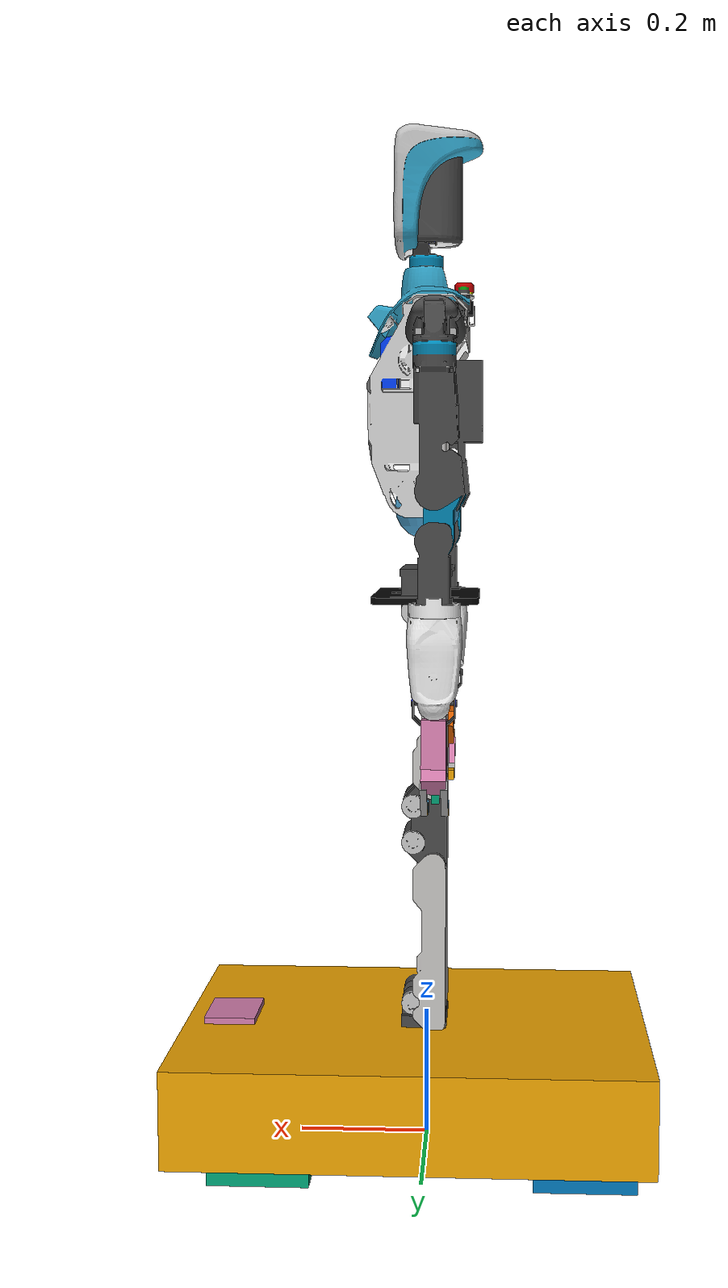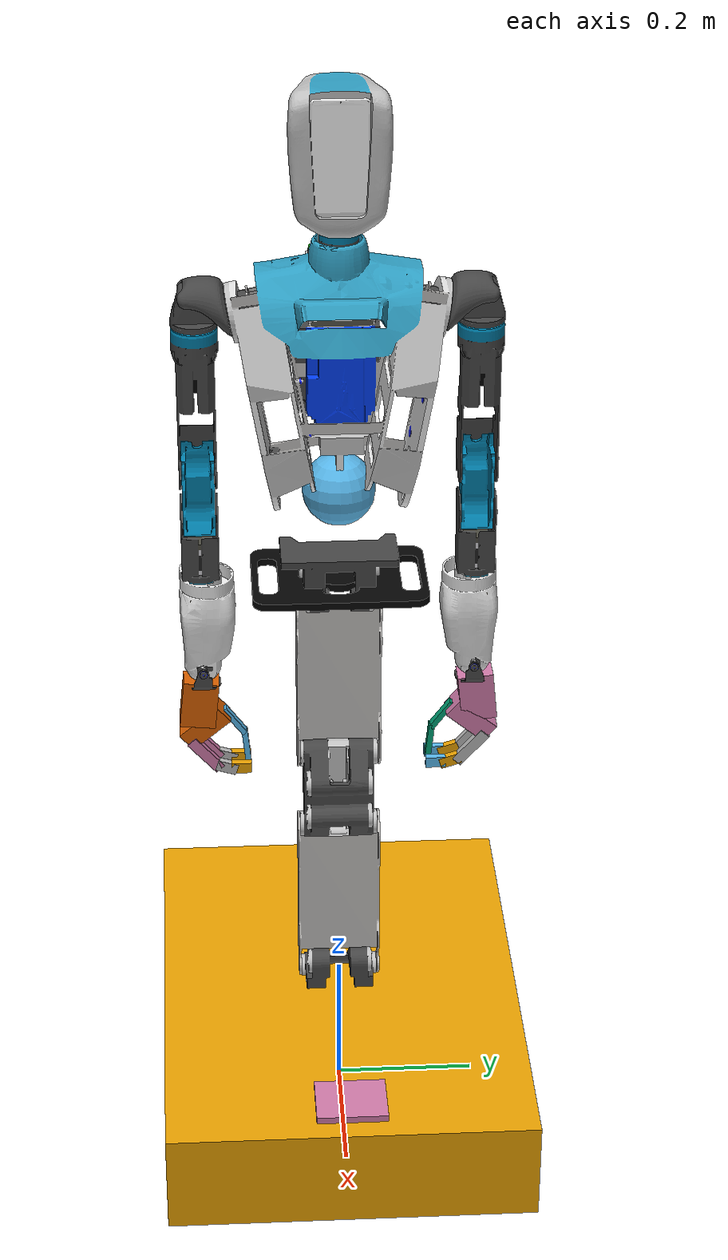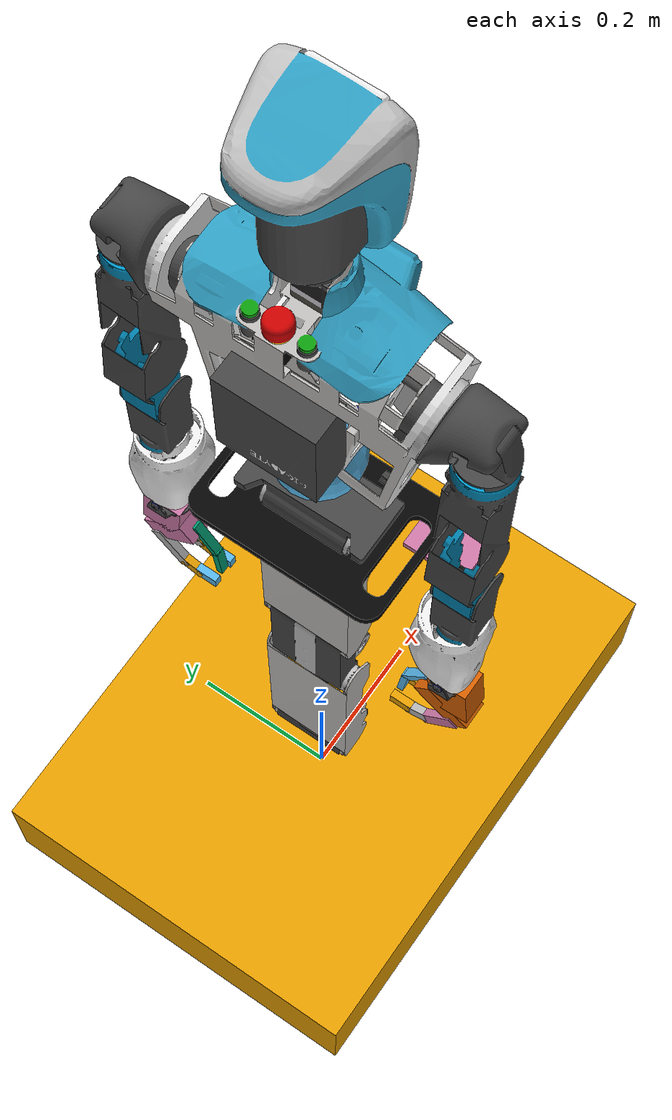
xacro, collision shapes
<?xml version="1.0"?>
<robot name="SEED-Noid-Mover-typeG" xmlns:xacro="http://ros.org/wiki/xacro">

  <!-- The following included files set up definitions of parts of the robot body -->
  <!-- wraps upperbody and hand-->
  <xacro:include filename="$(find seed_r7_description)/typeg/noid-upper.urdf.xacro" />
  <!-- wraps lifter and wheels-->
  <xacro:include filename="$(find seed_r7_description)/typeg/noid-wheels.urdf.xacro" />

 <!-- Now we can start using the macros included above to define the actual robot -->
 <xacro:noid-upper/>
 <xacro:noid-wheels base_link="base_link"/>

 <!-- gazebo settings -->
 <!-- camera -->

<xacro:property  name="camera_name" value="front_camera"/>
<link name="${camera_name}_depth_optical_frame"/>
<joint name="${camera_name}_depth_optical_joint" type="fixed">
  <origin xyz="0 0 0" rpy="${-M_PI/2} 0 ${-M_PI/2}" />
  <parent link="${camera_name}_link" />
  <child link="${camera_name}_depth_optical_frame" />
</joint>
<xacro:gazebo_depth_camera link_name="${camera_name}_link"
                      frame_name="${camera_name}_depth_optical_frame"
                      camera_name="${camera_name}"/>

<xacro:property  name="camera_name" value="rear_camera"/>
<link name="${camera_name}_depth_optical_frame"/>
<joint name="${camera_name}_depth_optical_joint" type="fixed">
  <origin xyz="0 0 0" rpy="${-M_PI/2} 0 ${-M_PI/2}" />
  <parent link="${camera_name}_link" />
  <child link="${camera_name}_depth_optical_frame" />
</joint>
<xacro:gazebo_depth_camera link_name="${camera_name}_link"
                      frame_name="${camera_name}_depth_optical_frame"
                      camera_name="${camera_name}"/>

<xacro:property  name="camera_name" value="chest_camera"/>
<link name="${camera_name}_depth_optical_frame"/>
<joint name="${camera_name}_depth_optical_joint" type="fixed">
  <origin xyz="0 0 0" rpy="${-M_PI/2} 0 ${-M_PI/2}" />
  <parent link="${camera_name}_link" />
  <child link="${camera_name}_depth_optical_frame" />
</joint>
<xacro:gazebo_depth_camera link_name="${camera_name}_link"
                      frame_name="${camera_name}_depth_optical_frame"
                      camera_name="${camera_name}"/>

 <!-- laser -->
 <xacro:gazebo_laser_sensor link_name="wheels_base_laser_link"
                            frame_name="wheels_base_laser_link" />

 <!-- joint control -->
 <xacro:gazebo_trajectory_controller />

 <!-- mobile base -->
 <xacro:gazebo_base_controller base_frame="base_link" />

 <!-- mimic joints -->
 <gazebo>
   <plugin name="mimic_updater" filename="libmimic_plugin.so">
     <!-- lifter -->
     <mimic joint="knee_joint"  offset="0.0" multiplier="-1.0"
            P="100" I="0.1" D="10" i_max="500" i_min="-500"
            command_max="2000" command_min="-2000" velocity='true'>
       knee_joint_mimic
     </mimic>
     <mimic joint="ankle_joint"  offset="0.0" multiplier="-1.0"
            P="100" I="0.1" D="10" i_max="500" i_min="-500"
            command_max="2000" command_min="-2000" velocity='true'>
       ankle_joint_mimic
     </mimic>
     <!-- lifter(dummy) -->
     <mimic joint="knee_joint"  offset="0.0" multiplier="-1.0"
            P="100" I="0.0" D="10" i_max="0" i_min="0"
            command_max="200" command_min="-200" velocity='true'>
       knee_joint_dummy
     </mimic>
     <mimic joint="ankle_joint"  offset="0.0" multiplier="1.0"
            P="100" I="0.0" D="10" i_max="0" i_min="0"
            command_max="200" command_min="-200"  velocity='true'>
       ankle_joint_dummy
     </mimic>

     <!-- lhand -->
     <mimic joint="l_thumb_joint"  offset="0.0" multiplier="-1.0"
            P="30" I="0.0" D="0.03" i_max="0" i_min="0"
            command_max="50" command_min="-50">
       l_indexbase_joint
     </mimic>
     <mimic joint="l_thumb_joint"  offset="-0.2" multiplier="-0.3"
            P="30" I="0.0" D="0.03" i_max="0" i_min="0"
            command_max="50" command_min="-50">
       l_indexmid_joint
     </mimic>
     <mimic joint="l_thumb_joint"  offset="-0.2" multiplier="-0.3"
            P="30" I="0.0" D="0.03" i_max="0" i_min="0"
            command_max="50" command_min="-50">
       l_indexend_joint
     </mimic>
     <!-- rhand -->
     <mimic joint="r_thumb_joint"  offset="0.0" multiplier="-1.0"
            P="30" I="0.0" D="0.03" i_max="0" i_min="0"
            command_max="50" command_min="-50">
       r_indexbase_joint
     </mimic>
     <mimic joint="r_thumb_joint"  offset="0.2" multiplier="-0.3"
            P="30" I="0.0" D="0.03" i_max="0" i_min="0"
            command_max="50" command_min="-50">
       r_indexmid_joint
     </mimic>
     <mimic joint="r_thumb_joint"  offset="0.2" multiplier="-0.3"
            P="30" I="0.0" D="0.03" i_max="0" i_min="0"
            command_max="50" command_min="-50">
       r_indexend_joint
     </mimic>

      <!-- r_elbow -->
     <mimic joint="r_elbow_joint"  offset="0.0" multiplier="-1.0"
            P="100" I="0.01" D="10" i_max="0" i_min="-0"
            command_max="50" command_min="-50" velocity='true'>
       r_elbow_joint_mimic
     </mimic>

     <mimic joint="r_elbow_joint"  offset="0.0" multiplier="0.591"
            P="100" I="0.01" D="10" i_max="0" i_min="-0"
            command_max="50" command_min="-50" velocity='true'>
       r_elbow_middle_joint
     </mimic>

     <mimic joint="r_elbow_joint"  offset="0.0" multiplier="0.409"
            P="100" I="0.01" D="10" i_max="0" i_min="-0"
            command_max="50" command_min="-50" velocity='true'>
       r_elbow_middle_joint_mimic
     </mimic>

     <!-- l_elbow -->
     <mimic joint="l_elbow_joint"  offset="0.0" multiplier="-1.0"
            P="100" I="0.01" D="10" i_max="0" i_min="-0"
            command_max="50" command_min="-50" velocity='true'>
       l_elbow_joint_mimic
     </mimic>

     <mimic joint="l_elbow_joint"  offset="0.0" multiplier="0.591"
            P="100" I="0.01" D="10" i_max="0" i_min="-0"
            command_max="50" command_min="-50" velocity='true'>
       l_elbow_middle_joint
     </mimic>

     <mimic joint="l_elbow_joint"  offset="0.0" multiplier="0.409"
            P="100" I="0.01" D="10" i_max="0" i_min="-0"
            command_max="50" command_min="-50" velocity='true'>
       l_elbow_middle_joint_mimic
     </mimic>

   </plugin>
 </gazebo>

</robot>

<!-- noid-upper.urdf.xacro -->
<!-- XML namespaces -->
<robot name="noid-upper" xmlns:xacro="http://ros.org/wiki/xacro">

  <xacro:include filename="$(find seed_r7_description)/urdf/typeG_upperbody/noid_upper_typeg.urdf.xacro" />
  <xacro:include filename="$(find seed_r7_description)/urdf/trx_s/trx_s.urdf.xacro" />

  <xacro:macro name="noid-upper" params="disable_mesh:=false">

  <xacro:noid_upper base_link="waist_link" r_hand_link="r_hand_link" l_hand_link="l_hand_link" disable_mesh="${disable_mesh}"/>

  <xacro:trx_s prefix="r" reflect="1" disable_mesh="${disable_mesh}"/>
  <xacro:trx_s prefix="l" reflect="-1" disable_mesh="${disable_mesh}"/>

  <joint name="upper_lower_connector" type="fixed">
    <parent link="lifter_top_link"/>
    <child link="waist_link"/>
    <origin xyz="0.0 0.0 0.0" rpy="0 0 0 "/>
  </joint>

  </xacro:macro>

</robot>

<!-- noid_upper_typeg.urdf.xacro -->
<!-- XML namespaces -->
<robot name="noid_upper_typeg" xmlns:xacro="http://ros.org/wiki/xacro">

  <xacro:include filename="$(find seed_r7_description)/urdf/gazebo.xacro" />

  <xacro:property name="wrist_sensor_offset" value="0.0"/>

  <xacro:macro name="noid_upper" params="base_link disable_mesh:=false r_hand_link:=r_hand_link l_hand_link:=l_hand_link">
  <!-- ============================   typeG_upper   ============================ -->
  <link name="${base_link}">
    <xacro:unless value="${disable_mesh}"> <visual>
      <origin xyz="0 0 0" rpy="0 0 0"/>
      <geometry>
        <mesh filename="package://seed_r7_description/meshes/typeG_upperbody/waist_link.dae" scale="1 1 1" />
      </geometry>
    </visual> </xacro:unless>
    <xacro:unless value="${disable_mesh}"> <collision>
      <origin xyz="0 0 0" rpy="0 -0 0"/>
      <geometry>
        <mesh filename="package://seed_r7_description/meshes/typeG_upperbody/waist_link.dae" scale="1 1 1" />
      </geometry>
    </collision> </xacro:unless>
    <inertial>
      <mass value="1.257" />
      <origin xyz="0 0 0.0" rpy="0 0 0"/>
      <inertia ixx="0.034" ixy="0" ixz="0" iyy="0.034" iyz="0" izz="0.018"/>
    </inertial>
  </link>
  <xacro:gazebo_link_reference link_name="${base_link}" />

  <link name="hip_sphere_link">
    <xacro:unless value="${disable_mesh}"> <visual>
      <origin xyz="0 0 0" rpy="0 0 0"/>
      <geometry>
        <mesh filename="package://seed_r7_description/meshes/typeG_upperbody/hip_sphere_link.dae" scale="1 1 1" />
      </geometry>
    </visual> </xacro:unless>
    <xacro:unless value="${disable_mesh}"> <collision>
      <origin xyz="0 0 0.132" rpy="0 0 0"/>
      <geometry>
        <sphere radius="0.05"/>
      </geometry>
    </collision> </xacro:unless>
    <inertial>
      <mass value="1.257" />
      <origin xyz="0 0 0.042" rpy="0 -0 0"/>
      <!-- inertia ixx="0.034" ixy="0" ixz="0" iyy="0.034" iyz="0" izz="0.018"/ -->
      <!-- just fixed for gazebo / reduce inertia-->
      <inertia ixx="0.01" ixy="0" ixz="0" iyy="0.01" iyz="0" izz="0.007"/>
    </inertial>
  </link>
  <xacro:gazebo_link_reference link_name="hip_sphere_link" />

  <link name="hip_center">
    <xacro:unless value="${disable_mesh}"> <visual>
      <origin xyz="0 0 0" rpy="0 0 0"/>
      <geometry>
        <mesh filename="package://seed_r7_description/meshes/typeG_upperbody/hip_center_link.dae" scale="1 1 1" />
      </geometry>
    </visual> </xacro:unless>
    <xacro:unless value="${disable_mesh}"> <collision>
      <origin xyz="0 0 0" rpy="0 0 0"/>
      <geometry>
        <sphere radius="0.05"/>
      </geometry>
    </collision> </xacro:unless>
    <inertial>
      <mass value="0.1" />
      <origin xyz="0 0 0" rpy="0 0 0"/>
      <inertia ixx="0.003" ixy="0" ixz="0" iyy="0.003" iyz="0" izz="0.003"/>
    </inertial>
  </link>
  <xacro:gazebo_link_reference link_name="hip_center" />

  <link name="body_link">
    <xacro:unless value="${disable_mesh}"> <visual>
      <origin xyz="0 0 0" rpy="0 0 0"/>
      <geometry>
        <mesh filename="package://seed_r7_description/meshes/typeG_upperbody/body_link.dae" scale="1 1 1" />
      </geometry>
    </visual> </xacro:unless>
    <xacro:unless value="${disable_mesh}"> <collision>
      <origin xyz="0 0 0" rpy="0 0 0"/>
      <geometry>
        <mesh filename="package://seed_r7_description/meshes/typeG_upperbody/body_link.dae" scale="1 1 1" />
      </geometry>
    </collision> </xacro:unless>
    <inertial>
      <mass value="10.551" />
      <origin xyz="0 0 0.22" rpy="0 -0 0"/>
      <inertia ixx="0.13" ixy="0" ixz="0" iyy="0.12" iyz="0" izz="0.114"/>
    </inertial>
  </link>
  <xacro:gazebo_link_reference link_name="body_link" />

  <link name="l_shoulder_link">
    <xacro:unless value="${disable_mesh}"> <visual>
      <origin xyz="0 0 0" rpy="0 0 0"/>
      <geometry>
        <mesh filename="package://seed_r7_description/meshes/typeG_upperbody/l_shoulder_link.dae" scale="1 1 1" />
      </geometry>
    </visual> </xacro:unless>
    <xacro:unless value="${disable_mesh}"> <collision>
      <origin xyz="0 0 0" rpy="0 0 0"/>
      <geometry>
        <mesh filename="package://seed_r7_description/meshes/typeG_upperbody/l_shoulder_link.dae" scale="1 1 1" />
      </geometry>
    </collision> </xacro:unless>
    <inertial>
      <mass value="0.242" />
      <!-- just fixed for gazebo / increase inertia-->
      <origin xyz="0 0.02 0.015" rpy="0 -0 0"/>
      <inertia ixx="0.00133" ixy="0" ixz="0" iyy="0.001" iyz="0" izz="0.00133"/>
    </inertial>
  </link>
  <xacro:gazebo_link_reference link_name="l_shoulder_link" />

  <link name="l_shoulder_center">
    <xacro:unless value="${disable_mesh}"> <visual>
      <origin xyz="0 0 0" rpy="0 -0 0"/>
      <geometry>
        <mesh filename="package://seed_r7_description/meshes/typeG_upperbody/l_shoulder_center_link.dae" scale="1 1 1" />
      </geometry>
    </visual> </xacro:unless>
    <xacro:unless value="${disable_mesh}"> <collision>
      <origin xyz="0 0 0" rpy="0 -0 0"/>
      <geometry>
        <mesh filename="package://seed_r7_description/meshes/typeG_upperbody/l_shoulder_center_link.dae" scale="1 1 1" />
      </geometry>
    </collision> </xacro:unless>
    <inertial>
      <mass value="0.744" />
      <!--origin xyz="0 0.01 0" rpy="0 -0 0"/-->
      <origin xyz="0 -0.01 -0.06" rpy="0 -0 0"/>
      <inertia ixx="0.000841" ixy="0" ixz="0" iyy="0.000835" iyz="0" izz="0.000304"/>
    </inertial>
  </link>
  <xacro:gazebo_link_reference link_name="l_shoulder_center" />

  <link name="l_upperarm_link">
    <xacro:unless value="${disable_mesh}"> <visual>
      <origin xyz="0 0 0" rpy="0 -0 0"/>
      <geometry>
        <mesh filename="package://seed_r7_description/meshes/typeG_upperbody/upperarm_link.dae" scale="1 1 1" />
      </geometry>
    </visual> </xacro:unless>
    <xacro:unless value="${disable_mesh}"> <collision>
      <origin xyz="0 0 0" rpy="0 -0 0"/>
      <geometry>
        <mesh filename="package://seed_r7_description/meshes/typeG_upperbody/upperarm_link.dae" scale="1 1 1" />
      </geometry>
    </collision> </xacro:unless>
    <inertial>
      <mass value="0.574" />
      <!-- fix for gazebo -->
      <origin xyz="0.005 0 -0.0654" rpy="0 -0 0"/>
      <inertia ixx="0.00214" ixy="0" ixz="0" iyy="0.00217" iyz="0" izz="0.003"/>
    </inertial>
  </link>
  <xacro:gazebo_link_reference link_name="l_upperarm_link" />

  <link name="l_elbow_virtual_link">
    <inertial>
      <mass value="0.001" />
      <origin xyz="0 0 0" rpy="0 0 0"/>
      <inertia ixx="0.01" ixy="0" ixz="0" iyy="0.01" iyz="0" izz="0.01"/>
    </inertial>
  </link>
  <xacro:gazebo_link_reference link_name="l_elbow_virtual_link" />

  <link name="l_elbow_virtual_link_dummy">
    <inertial>
      <mass value="0.001" />
      <origin xyz="0 0 0" rpy="0 0 0"/>
      <inertia ixx="0.01" ixy="0" ixz="0" iyy="0.01" iyz="0" izz="0.01"/>
    </inertial>
  </link>
  <xacro:gazebo_link_reference link_name="l_elbow_virtual_link_dummy" />

  <link name="l_elbow_middle_link">
    <xacro:unless value="${disable_mesh}"> <visual>
      <origin xyz="0 0 0" rpy="0 -0 0"/>
      <geometry>
        <mesh filename="package://seed_r7_description/meshes/typeG_upperbody/elbow_middle_link.dae" scale="1 1 1" />
      </geometry>
    </visual> </xacro:unless>
    <xacro:unless value="${disable_mesh}"> <collision>
      <origin xyz="0 0 0" rpy="0 -0 0"/>
      <geometry>
        <mesh filename="package://seed_r7_description/meshes/typeG_upperbody/elbow_middle_link.dae" scale="1 1 1" />
      </geometry>
    </collision> </xacro:unless>
    <inertial>
      <mass value="0.162" />
      <origin xyz="-0.014 0 -0.032" rpy="0 -0 0"/>
      <inertia ixx="0.00178" ixy="0" ixz="0" iyy="0.00179" iyz="0" izz="0.0035"/>
    </inertial>
  </link>
  <xacro:gazebo_link_reference link_name="l_elbow_middle_link" />

  <link name="l_elbow_link">
    <xacro:unless value="${disable_mesh}"> <visual>
      <origin xyz="0 0 0" rpy="0 -0 0"/>
      <geometry>
        <mesh filename="package://seed_r7_description/meshes/typeG_upperbody/elbow_link.dae" scale="1 1 1" />
      </geometry>
    </visual> </xacro:unless>
    <xacro:unless value="${disable_mesh}"> <collision>
      <origin xyz="0 0 0" rpy="0 -0 0"/>
      <geometry>
        <mesh filename="package://seed_r7_description/meshes/typeG_upperbody/elbow_link.dae" scale="1 1 1" />
      </geometry>
    </collision> </xacro:unless>
    <inertial>
      <mass value="0.711" />
      <!-- fix for gazebo -->
      <origin xyz="-0.03 0 -0.0546" rpy="0 -0 0"/>
      <inertia ixx="0.00178" ixy="0" ixz="0" iyy="0.00179" iyz="0" izz="0.0035"/>
    </inertial>
  </link>
  <xacro:gazebo_link_reference link_name="l_elbow_link" />

  <link name="l_forearm_link">
    <xacro:unless value="${disable_mesh}"> <visual>
      <origin xyz="0 0 0" rpy="0 0 0"/>
      <geometry>
        <mesh filename="package://seed_r7_description/meshes/typeG_upperbody/l_forearm_link.dae" scale="1 1 1" />
      </geometry>
    </visual> </xacro:unless>
    <xacro:unless value="${disable_mesh}"> <collision>
      <origin xyz="0 0 0" rpy="0 0 0"/>
      <geometry>
        <mesh filename="package://seed_r7_description/meshes/typeG_upperbody/l_forearm_link.dae" scale="1 1 1" />
      </geometry>
    </collision> </xacro:unless>
    <inertial>
      <mass value="0.132" />
      <origin xyz="0.006 0 -0.0738" rpy="0 -0 0"/>
      <!--inertia ixx="0.00276" ixy="0" ixz="0" iyy="0.00286" iyz="0" izz="0.004"/-->
      <inertia ixx="0.0007" ixy="0" ixz="0" iyy="0.0007" iyz="0" izz="0.0004"/>
    </inertial>
  </link>
  <xacro:gazebo_link_reference link_name="l_forearm_link" />

  <link name="l_wrist_center">
    <xacro:unless value="${disable_mesh}"> <visual>
      <origin xyz="0 0 0" rpy="0 0 0"/>
      <geometry>
        <mesh filename="package://seed_r7_description/meshes/typeG_upperbody/l_wrist_center_link.dae" scale="1 1 1" />
      </geometry>
    </visual> </xacro:unless>
    <xacro:unless value="${disable_mesh}"> <collision>
      <origin xyz="0 0 0" rpy="0 0 0"/>
      <geometry>
        <mesh filename="package://seed_r7_description/meshes/typeG_upperbody/l_wrist_center_link.dae" scale="1 1 1" />
      </geometry>
    </collision> </xacro:unless>
    <inertial>
      <mass value="0.05" />
      <origin xyz="0 0 0" rpy="0 -0 0"/>
      <inertia ixx="0.0001" ixy="0" ixz="0" iyy="0.0001" iyz="0" izz="0.0001"/>
    </inertial>
  </link>
  <xacro:gazebo_link_reference link_name="l_wrist_center" />

  <link name="l_wrist_r_link">
    <xacro:unless value="${disable_mesh}"> <visual>
      <origin xyz="0 0 0" rpy="0 0 0"/>
      <geometry>
        <mesh filename="package://seed_r7_description/meshes/typeG_upperbody/l_wrist_r_link.dae" scale="1 1 1" />
      </geometry>
    </visual> </xacro:unless>
    <xacro:unless value="${disable_mesh}"> <collision>
      <origin xyz="0 0 0" rpy="0 0 0"/>
      <geometry>
        <mesh filename="package://seed_r7_description/meshes/typeG_upperbody/l_wrist_r_link.dae" scale="1 1 1" />
      </geometry>
    </collision> </xacro:unless>
    <inertial>
      <mass value="0.05" />
      <origin xyz="0 0 0" rpy="0 -0 0"/>
      <inertia ixx="0.0001" ixy="0" ixz="0" iyy="0.0001" iyz="0" izz="0.0001"/>
    </inertial>
  </link>
  <xacro:gazebo_link_reference link_name="l_wrist_r_link" />

  <link name="neck_link">
    <xacro:unless value="${disable_mesh}"> <visual>
      <origin xyz="0 0 0" rpy="0 -0 0"/>
      <geometry>
        <mesh filename="package://seed_r7_description/meshes/typeG_upperbody/neck_link.dae" scale="1 1 1" />
      </geometry>
    </visual> </xacro:unless>
    <xacro:unless value="${disable_mesh}"> <collision>
      <origin xyz="0 0 0" rpy="0 -0 0"/>
      <geometry>
        <mesh filename="package://seed_r7_description/meshes/typeG_upperbody/neck_link.dae" scale="1 1 1" />
      </geometry>
    </collision> </xacro:unless>
    <inertial>
      <mass value="0.341" />
      <origin xyz="0 0 0.0595" rpy="0 -0 0"/>
      <!--inertia ixx="1.64186e-35" ixy="0" ixz="0" iyy="1.64186e-35" iyz="0" izz="0"/-->
      <inertia ixx="0.001" ixy="0" ixz="0" iyy="0.001" iyz="0" izz="0.002"/>
    </inertial>
  </link>
  <xacro:gazebo_link_reference link_name="neck_link" />

  <link name="head_base_link">
    <xacro:unless value="${disable_mesh}"> <visual>
      <origin xyz="0 0 0" rpy="0 -0 0"/>
      <geometry>
        <mesh filename="package://seed_r7_description/meshes/typeG_upperbody/head_base_link.dae" scale="1 1 1" />
      </geometry>
    </visual> </xacro:unless>
    <xacro:unless value="${disable_mesh}"> <collision>
      <origin xyz="0 0 0" rpy="0 -0 0"/>
      <geometry>
        <mesh filename="package://seed_r7_description/meshes/typeG_upperbody/head_base_link.dae" scale="1 1 1" />
      </geometry>
    </collision> </xacro:unless>
    <inertial>
      <mass value="0.1" />
      <origin xyz="0 0 0" rpy="0 -0 0"/>
      <inertia ixx="0.0005" ixy="0" ixz="0" iyy="0.0005" iyz="0" izz="0.0005"/>
    </inertial>
  </link>
  <xacro:gazebo_link_reference link_name="head_base_link" />

  <link name="head_link">
    <xacro:unless value="${disable_mesh}"> <visual>
      <origin xyz="0 0 0" rpy="0 -0 0"/>
      <geometry>
        <mesh filename="package://seed_r7_description/meshes/typeG_upperbody/head_link.dae" scale="1 1 1" />
      </geometry>
    </visual> </xacro:unless>
    <xacro:unless value="${disable_mesh}"> <collision>
      <origin xyz="0 0 0" rpy="0 -0 0"/>
      <geometry>
        <mesh filename="package://seed_r7_description/meshes/typeG_upperbody/head_link.dae" scale="1 1 1" />
      </geometry>
    </collision> </xacro:unless>
    <inertial>
      <mass value="0.974" />
      <origin xyz="0.01 0 0.070" rpy="0 -0 0"/>
      <inertia ixx="0.005" ixy="0" ixz="0" iyy="0.005" iyz="0" izz="0.005"/>
    </inertial>
  </link>
  <xacro:gazebo_link_reference link_name="head_link" />

  <link name="r_shoulder_link">
    <xacro:unless value="${disable_mesh}"> <visual>
      <origin xyz="0 0 0" rpy="0 0 0"/>
      <geometry>
        <mesh filename="package://seed_r7_description/meshes/typeG_upperbody/r_shoulder_link.dae" scale="1 1 1" />
      </geometry>
    </visual> </xacro:unless>
    <xacro:unless value="${disable_mesh}"> <collision>
      <origin xyz="0 0 0" rpy="0 0 0"/>
      <geometry>
        <mesh filename="package://seed_r7_description/meshes/typeG_upperbody/r_shoulder_link.dae" scale="1 1 1" />
      </geometry>
    </collision> </xacro:unless>
    <inertial>
      <mass value="0.242" />
      <origin xyz="0 -0.02 0.015" rpy="0 -0 0"/>
      <inertia ixx="0.00133" ixy="0" ixz="0" iyy="0.001" iyz="0" izz="0.00133"/>
    </inertial>
  </link>
  <xacro:gazebo_link_reference link_name="r_shoulder_link" />

  <link name="r_shoulder_center">
    <xacro:unless value="${disable_mesh}"> <visual>
      <origin xyz="0 0 0" rpy="0 -0 0"/>
      <geometry>
        <mesh filename="package://seed_r7_description/meshes/typeG_upperbody/r_shoulder_center_link.dae" scale="1 1 1" />
      </geometry>
    </visual> </xacro:unless>
    <xacro:unless value="${disable_mesh}"> <collision>
      <origin xyz="0 0 0" rpy="0 -0 0"/>
      <geometry>
        <mesh filename="package://seed_r7_description/meshes/typeG_upperbody/r_shoulder_center_link.dae" scale="1 1 1" />
      </geometry>
    </collision> </xacro:unless>
    <inertial>
      <mass value="0.744" />
      <!--origin xyz="0 -0.01 0" rpy="0 -0 0"/-->
      <origin xyz="0 0.01 -0.06" rpy="0 -0 0"/>
      <inertia ixx="0.000841" ixy="0" ixz="0" iyy="0.000835" iyz="0" izz="0.000305"/>
    </inertial>
  </link>
  <xacro:gazebo_link_reference link_name="r_shoulder_center" />

  <link name="r_upperarm_link">
    <xacro:unless value="${disable_mesh}"> <visual>
      <origin xyz="0 0 0" rpy="0 -0 0"/>
      <geometry>
        <mesh filename="package://seed_r7_description/meshes/typeG_upperbody/upperarm_link.dae" scale="1 1 1" />
      </geometry>
    </visual> </xacro:unless>
    <xacro:unless value="${disable_mesh}"> <collision>
      <origin xyz="0 0 0" rpy="0 -0 0"/>
      <geometry>
        <mesh filename="package://seed_r7_description/meshes/typeG_upperbody/upperarm_link.dae" scale="1 1 1" />
      </geometry>
    </collision> </xacro:unless>
    <inertial>
      <mass value="0.574" />
      <!-- fix for gazebo -->
      <origin xyz="0.005 0 -0.0654" rpy="0 -0 0"/>
      <inertia ixx="0.00214" ixy="0" ixz="0" iyy="0.00217" iyz="0" izz="0.003"/>
    </inertial>
  </link>
  <xacro:gazebo_link_reference link_name="r_upperarm_link" />

  <link name="r_elbow_virtual_link">
    <inertial>
      <mass value="0.001" />
      <origin xyz="0 0 0" rpy="0 0 0"/>
      <inertia ixx="0.01" ixy="0" ixz="0" iyy="0.01" iyz="0" izz="0.01"/>
    </inertial>
  </link>
  <xacro:gazebo_link_reference link_name="r_elbow_virtual_link" />

  <link name="r_elbow_virtual_link_dummy">
    <inertial>
      <mass value="0.001" />
      <origin xyz="0 0 0" rpy="0 0 0"/>
      <inertia ixx="0.01" ixy="0" ixz="0" iyy="0.01" iyz="0" izz="0.01"/>
    </inertial>
  </link>
  <xacro:gazebo_link_reference link_name="r_elbow_virtual_link_dummy" />

  <link name="r_elbow_middle_link">
    <xacro:unless value="${disable_mesh}"> <visual>
      <origin xyz="0 0 0" rpy="0 -0 0"/>
      <geometry>
        <mesh filename="package://seed_r7_description/meshes/typeG_upperbody/elbow_middle_link.dae" scale="1 1 1" />
      </geometry>
    </visual> </xacro:unless>
    <xacro:unless value="${disable_mesh}"> <collision>
      <origin xyz="0 0 0" rpy="0 -0 0"/>
      <geometry>
        <mesh filename="package://seed_r7_description/meshes/typeG_upperbody/elbow_middle_link.dae" scale="1 1 1" />
      </geometry>
    </collision> </xacro:unless>
    <inertial>
      <mass value="0.162" />
      <origin xyz="-0.014 0 -0.032" rpy="0 -0 0"/>
      <inertia ixx="0.00178" ixy="0" ixz="0" iyy="0.00179" iyz="0" izz="0.0035"/>
    </inertial>
  </link>
  <xacro:gazebo_link_reference link_name="r_elbow_middle_link" />

  <link name="r_elbow_link">
    <xacro:unless value="${disable_mesh}"> <visual>
      <origin xyz="0 0 0" rpy="0 -0 0"/>
      <geometry>
        <mesh filename="package://seed_r7_description/meshes/typeG_upperbody/elbow_link.dae" scale="1 1 1" />
      </geometry>
    </visual> </xacro:unless>
    <xacro:unless value="${disable_mesh}"> <collision>
      <origin xyz="0 0 0" rpy="0 -0 0"/>
      <geometry>
        <mesh filename="package://seed_r7_description/meshes/typeG_upperbody/elbow_link.dae" scale="1 1 1" />
      </geometry>
    </collision> </xacro:unless>
    <inertial>
      <mass value="0.711" />
      <!-- fix for gazebo -->
      <origin xyz="-0.03 0 -0.0546" rpy="0 -0 0"/>
      <inertia ixx="0.00178" ixy="0" ixz="0" iyy="0.00179" iyz="0" izz="0.0035"/>
    </inertial>
  </link>
  <xacro:gazebo_link_reference link_name="r_elbow_link" />

  <link name="r_forearm_link">
    <xacro:unless value="${disable_mesh}"> <visual>
      <origin xyz="0 0 0" rpy="0 0 0"/>
      <geometry>
        <mesh filename="package://seed_r7_description/meshes/typeG_upperbody/r_forearm_link.dae" scale="1 1 1" />
      </geometry>
    </visual> </xacro:unless>
    <xacro:unless value="${disable_mesh}"> <collision>
      <origin xyz="0 0 0" rpy="0 0 0"/>
      <geometry>
        <mesh filename="package://seed_r7_description/meshes/typeG_upperbody/r_forearm_link.dae" scale="1 1 1" />
      </geometry>
    </collision> </xacro:unless>
    <inertial>
      <mass value="0.132" />
      <origin xyz="0.006 0 -0.0738" rpy="0 -0 0"/>
      <!--inertia ixx="0.00276" ixy="0" ixz="0" iyy="0.00286" iyz="0" izz="0.004"/-->
      <inertia ixx="0.0007" ixy="0" ixz="0" iyy="0.0007" iyz="0" izz="0.0004"/>
    </inertial>
  </link>
  <xacro:gazebo_link_reference link_name="r_forearm_link" />

  <link name="r_wrist_center">
    <xacro:unless value="${disable_mesh}"> <visual>
      <origin xyz="0 0 0" rpy="0 0 0"/>
      <geometry>
        <mesh filename="package://seed_r7_description/meshes/typeG_upperbody/r_wrist_center_link.dae" scale="1 1 1" />
      </geometry>
    </visual> </xacro:unless>
    <xacro:unless value="${disable_mesh}"> <collision>
      <origin xyz="0 0 0" rpy="0 0 0"/>
      <geometry>
        <mesh filename="package://seed_r7_description/meshes/typeG_upperbody/r_wrist_center_link.dae" scale="1 1 1" />
      </geometry>
    </collision> </xacro:unless>
    <inertial>
      <mass value="0.05" />
      <origin xyz="0 0 0" rpy="0 -0 0"/>
      <inertia ixx="0.0001" ixy="0" ixz="0" iyy="0.0001" iyz="0" izz="0.0001"/>
    </inertial>
  </link>
  <xacro:gazebo_link_reference link_name="r_wrist_center" />

  <link name="r_wrist_r_link">
    <xacro:unless value="${disable_mesh}"> <visual>
      <origin xyz="0 0 0" rpy="0 0 0"/>
      <geometry>
        <mesh filename="package://seed_r7_description/meshes/typeG_upperbody/r_wrist_r_link.dae" scale="1 1 1" />
      </geometry>
    </visual> </xacro:unless>
    <xacro:unless value="${disable_mesh}"> <collision>
      <origin xyz="0 0 0" rpy="0 0 0"/>
      <geometry>
        <mesh filename="package://seed_r7_description/meshes/typeG_upperbody/r_wrist_r_link.dae" scale="1 1 1" />
      </geometry>
    </collision> </xacro:unless>
    <inertial>
      <mass value="0.05" />
      <origin xyz="0 0 0" rpy="0 -0 0"/>
      <inertia ixx="0.0001" ixy="0" ixz="0" iyy="0.0001" iyz="0" izz="0.0001"/>
    </inertial>
  </link>
  <xacro:gazebo_link_reference link_name="r_wrist_r_link" />

  <joint name="waist_y_joint" type="revolute">
    <parent link="${base_link}"/>
    <child  link="hip_sphere_link"/>
    <origin xyz="0 0 0.005" rpy="0 -0 0 "/>
    <axis   xyz="0 0 1"/>
    <!-- from -120 to 120 degrees-->
    <limit lower="-2.09" upper="2.09" effort="500" velocity="0.6" />
    <dynamics damping="0.2" friction="0" />
  </joint>
  <xacro:gazebo_transmission joint_name="waist_y_joint" />

  <joint name="waist_p_joint" type="revolute">
    <parent link="hip_sphere_link"/>
    <child  link="hip_center"/>
    <origin xyz="0 0 0.132" rpy="0 -0 0 "/>
    <axis   xyz="0 1 0"/>
    <!-- from -10 to 40 degrees-->
    <limit lower="-0.17" upper="0.69" effort="500" velocity="0.4" />
    <dynamics damping="0.2" friction="0" />
  </joint>
  <xacro:gazebo_transmission joint_name="waist_p_joint" />

  <joint name="waist_r_joint" type="revolute">
    <parent link="hip_center"/>
    <child  link="body_link"/>
    <origin xyz="0 0 0" rpy="0 -0 0 "/>
    <axis   xyz="1 0 0"/>
    <!-- from -7 to 7 degrees-->
    <limit lower="-0.12" upper="0.12" effort="500" velocity="0.3" />
    <dynamics damping="0.2" friction="0" />
  </joint>
  <xacro:gazebo_transmission joint_name="waist_r_joint" />

  <joint name="l_shoulder_p_joint" type="revolute">
    <parent link="body_link"/>
    <child  link="l_shoulder_link"/>
    <origin xyz="-0.018 0.134202 0.251871" rpy="0 0 0 "/>
    <axis   xyz="0 0.984808 -0.173648"/>
    <!-- from -89 to 17 degrees-->
    <limit lower="-1.55" upper="0.29" effort="200" velocity="0.4" />
    <dynamics damping="0.2" friction="0" />
  </joint>
  <xacro:gazebo_transmission joint_name="l_shoulder_p_joint" />

  <joint name="l_shoulder_r_joint" type="revolute">
    <parent link="l_shoulder_link"/>
    <child  link="l_shoulder_center"/>
    <origin xyz="0 0.064702 0.027177" rpy="0 0 0 "/>
    <axis   xyz="1 0 0"/>
    <!-- from -5 to 90 degrees-->
    <limit lower="-0.08" upper="1.57" effort="100" velocity="0.5" />
    <dynamics damping="0.2" friction="0" />
  </joint>
  <xacro:gazebo_transmission joint_name="l_shoulder_r_joint" />

  <joint name="l_shoulder_y_joint" type="revolute">
    <parent link="l_shoulder_center"/>
    <child  link="l_upperarm_link"/>
    <origin xyz="0 -0.01 -0.0455" rpy="0 -0 0 "/>
    <axis   xyz="0 0 1"/>
    <!-- from -90 to 90 degrees-->
    <limit lower="-1.57" upper="1.57" effort="100" velocity="1.1" />
    <dynamics damping="0.2" friction="0" />
  </joint>
  <xacro:gazebo_transmission joint_name="l_shoulder_y_joint" />

  <joint name="l_wrist_y_joint" type="revolute">
    <parent link="l_elbow_link"/>
    <child  link="l_forearm_link"/>
    <origin xyz="0.0 0 -0.1095" rpy="0 -0 0 "/>
    <axis   xyz="0 0 1"/>
    <!-- from -90 to 90 degrees-->
    <limit lower="-1.57" upper="1.57" effort="100" velocity="1.2" />
    <dynamics damping="0.2" friction="0" />
  </joint>
  <xacro:gazebo_transmission joint_name="l_wrist_y_joint" />

  <joint name="l_wrist_p_joint" type="revolute">
    <parent link="l_forearm_link"/>
    <child  link="l_wrist_center"/>
    <origin xyz="0 0 -0.124" rpy="0 -0 0 "/>
    <axis   xyz="0 1 0"/>
    <!-- from -7 to 7 degrees-->
    <limit lower="-0.12" upper="0.12" effort="100" velocity="0.8" />
    <dynamics damping="0.2" friction="0" />
  </joint>
  <xacro:gazebo_transmission joint_name="l_wrist_p_joint" />

  <joint name="l_wrist_r_joint" type="revolute">
    <parent link="l_wrist_center"/>
    <child  link="l_wrist_r_link"/>
    <origin xyz="0 0 0" rpy="0 -0 0 "/>
    <axis   xyz="1 0 0"/>
    <!-- from -90 to 20 degrees-->
    <limit lower="-1.57" upper="0.34" effort="100" velocity="1.8" />
    <dynamics damping="0.2" friction="0" />
  </joint>
  <xacro:gazebo_transmission joint_name="l_wrist_r_joint" />

  <joint name="l_wrist_to_hand_connector" type="fixed">
    <parent link="l_wrist_r_link"/>
    <child  link="${l_hand_link}"/>
    <origin xyz="0 0 -0.003" rpy="0 0 0 "/>
  </joint>

  <joint name="neck_y_joint" type="revolute">
    <parent link="body_link"/>
    <child  link="neck_link"/>
    <origin xyz="0.002 0 0.377" rpy="0 -0 0 "/>
    <axis   xyz="0 0 1"/>
    <!-- from -120 to 120 degrees-->
    <limit lower="-2.09" upper="2.09" effort="100" velocity="1.7" />
    <dynamics damping="0.2" friction="0" />
  </joint>
  <xacro:gazebo_transmission joint_name="neck_y_joint" />

  <joint name="neck_p_joint" type="revolute">
    <parent link="neck_link"/>
    <child  link="head_base_link"/>
    <!-- real x=0.015 but can't move by eef of head, so set below-->
    <origin xyz="0.0 0 0.0265" rpy="0 -0 0 "/>
    <axis   xyz="0 1 0"/>
    <!-- from -20 to 30 degrees-->
    <limit lower="-0.34" upper="0.52" effort="100" velocity="2.1" />
    <dynamics damping="0.2" friction="0" />
  </joint>
  <xacro:gazebo_transmission joint_name="neck_p_joint" />

  <joint name="neck_r_joint" type="revolute">
    <parent link="head_base_link"/>
    <child  link="head_link"/>
    <origin xyz="0 0 0" rpy="0 -0 0 "/>
    <axis   xyz="1 0 0"/>
    <!-- from -20 to 20 degrees-->
    <limit lower="-0.34" upper="0.34" effort="100" velocity="0.8" />
    <dynamics damping="0.2" friction="0" />
  </joint>
  <xacro:gazebo_transmission joint_name="neck_r_joint" />

  <joint name="r_shoulder_p_joint" type="revolute">
    <parent link="body_link"/>
    <child  link="r_shoulder_link"/>
    <origin xyz="-0.018 -0.134202 0.251871" rpy="0 -0 0 "/>
    <axis   xyz="0 0.984808 0.173648"/>
    <!-- from -89 to 17 degrees-->
    <limit lower="-1.55" upper="0.29" effort="200" velocity="0.4" />
    <dynamics damping="0.2" friction="0" />
  </joint>
  <xacro:gazebo_transmission joint_name="r_shoulder_p_joint" />

  <joint name="r_shoulder_r_joint" type="revolute">
    <parent link="r_shoulder_link"/>
    <child  link="r_shoulder_center"/>
    <origin xyz="0 -0.064702 0.027177" rpy="0 -0 0 "/>
    <axis   xyz="1 0 0"/>
    <!-- from -90 to 5 degrees-->
    <limit lower="-1.57" upper="0.08" effort="100" velocity="0.5" />
    <dynamics damping="0.2" friction="0" />
  </joint>
  <xacro:gazebo_transmission joint_name="r_shoulder_r_joint" />

  <joint name="r_shoulder_y_joint" type="revolute">
    <parent link="r_shoulder_center"/>
    <child  link="r_upperarm_link"/>
    <origin xyz="0 0.01 -0.0455" rpy="0 -0 0 "/>
    <axis   xyz="0 0 1"/>
    <!-- from -180 to 180 degrees-->
    <limit lower="-1.57" upper="1.57" effort="100" velocity="1.1" />
    <dynamics damping="0.2" friction="0" />
  </joint>
  <xacro:gazebo_transmission joint_name="r_shoulder_y_joint" />

  <joint name="r_wrist_y_joint" type="revolute">
    <parent link="r_elbow_link"/>
    <child  link="r_forearm_link"/>
    <origin xyz="0.0 0 -0.1095" rpy="0 -0 0 "/>
    <axis   xyz="0 0 1"/>
    <!-- from -90 to 90 degrees-->
    <limit lower="-1.57" upper="1.57" effort="100" velocity="1.2" />
    <dynamics damping="0.2" friction="0" />
  </joint>
  <xacro:gazebo_transmission joint_name="r_wrist_y_joint" />

  <joint name="r_wrist_p_joint" type="revolute">
    <parent link="r_forearm_link"/>
    <child  link="r_wrist_center"/>
    <origin xyz="0 0 -0.124" rpy="0 -0 0 "/>
    <axis   xyz="0 1 0"/>
    <!-- from -7 to 7 degrees-->
    <limit lower="-0.12" upper="0.12" effort="100" velocity="0.8" />
    <dynamics damping="0.2" friction="0" />
  </joint>
  <xacro:gazebo_transmission joint_name="r_wrist_p_joint" />

  <joint name="r_wrist_r_joint" type="revolute">
    <parent link="r_wrist_center"/>
    <child  link="r_wrist_r_link"/>
    <origin xyz="0 0 0" rpy="0 -0 0 "/>
    <axis   xyz="1 0 0"/>
    <!-- from -20 to 90 degrees-->
    <limit lower="-0.34" upper="1.57" effort="100" velocity="1.8" />
    <dynamics damping="0.2" friction="0" />
  </joint>
  <xacro:gazebo_transmission joint_name="r_wrist_r_joint" />

  <joint name="r_wrist_to_hand_connector" type="fixed">
    <parent link="r_wrist_r_link"/>
    <child  link="${r_hand_link}"/>
    <origin xyz="0 0 -0.003" rpy="0 0 0 "/>
  </joint>

  <joint name="r_elbow_joint" type="revolute">
    <parent link="r_upperarm_link"/>
    <child  link="r_elbow_virtual_link"/>
    <origin xyz="0.0 0 -0.2085" rpy="0 -0 0 "/>
    <axis   xyz="0 1 0"/>
    <!-- from -170 to 0 degrees-->
    <limit lower="-3.0" upper="0" effort="100" velocity="1.1" />
    <dynamics damping="0.2" friction="0.1" />
  </joint>
  <xacro:gazebo_transmission joint_name="r_elbow_joint" />

  <joint name="r_elbow_joint_mimic" type="continuous">
    <parent link="r_elbow_virtual_link"/>
    <child  link="r_elbow_virtual_link_dummy"/>
    <origin xyz="0.0 0 0" rpy="0 0 0 "/>
    <axis   xyz="0 1 0"/>
    <mimic joint="r_elbow_joint" multiplier="-1" offset="0" />
  </joint>

  <joint name="r_elbow_middle_joint" type="continuous">
    <parent link="r_elbow_virtual_link_dummy"/>
    <child  link="r_elbow_middle_link"/>
    <origin xyz="0.0 0 0" rpy="0 -0 0 "/>
    <axis   xyz="0 1 0"/>
    <mimic joint="r_elbow_joint" multiplier="0.591222" offset="0" />
  </joint>

  <joint name="r_elbow_middle_joint_mimic" type="continuous">
    <parent link="r_elbow_middle_link"/>
    <child  link="r_elbow_link"/>
    <origin xyz="0.0 0 -0.07" rpy="0 -0 0 "/>
    <axis   xyz="0 1 0"/>
    <mimic joint="r_elbow_joint" multiplier="0.408778" offset="0" />
  </joint>

  <joint name="l_elbow_joint" type="revolute">
    <parent link="l_upperarm_link"/>
    <child  link="l_elbow_virtual_link"/>
    <origin xyz="0.0 0 -0.2085" rpy="0 -0 0 "/>
    <axis   xyz="0 1 0"/>
    <!-- from -170 to 0 degrees-->
    <limit lower="-3.0" upper="0" effort="100" velocity="1.1" />
    <dynamics damping="0.2" friction="0.1" />
  </joint>
  <xacro:gazebo_transmission joint_name="l_elbow_joint" />

  <joint name="l_elbow_joint_mimic" type="continuous">
    <parent link="l_elbow_virtual_link"/>
    <child  link="l_elbow_virtual_link_dummy"/>
    <origin xyz="0.0 0 0" rpy="0 0 0 "/>
    <axis   xyz="0 1 0"/>
    <mimic joint="l_elbow_joint" multiplier="-1" offset="0" />
  </joint>

  <joint name="l_elbow_middle_joint" type="continuous">
    <parent link="l_elbow_virtual_link_dummy"/>
    <child  link="l_elbow_middle_link"/>
    <origin xyz="0.0 0 0" rpy="0 -0 0 "/>
    <axis   xyz="0 1 0"/>
    <mimic joint="l_elbow_joint" multiplier="0.591222" offset="0" />
  </joint>

  <joint name="l_elbow_middle_joint_mimic" type="continuous">
    <parent link="l_elbow_middle_link"/>
    <child  link="l_elbow_link"/>
    <origin xyz="0.0 0 -0.07" rpy="0 -0 0 "/>
    <axis   xyz="0 1 0"/>
    <mimic joint="l_elbow_joint" multiplier="0.408778" offset="0" />
  </joint>

  <link name="chest_camera_link"/>
  <joint name="body_link_to_chest_camera_link" type="fixed">
    <parent  link="body_link"/>
    <child link="chest_camera_link"/>
    <origin xyz="0.058198 0.0 0.273087" rpy="0 0.698132 0"/>
  </joint>

  <link name="chest_camera_right_ir_frame"/>
  <joint name="chest_camera_link_to_chest_camera_right_ir_link" type="fixed">
    <parent  link="chest_camera_link"/>
    <child link="chest_camera_right_ir_frame"/>
    <origin xyz="0 -0.055 0" rpy="0 0 0"/>  <!-- realsense d415-->
  </joint>

  </xacro:macro>
</robot>

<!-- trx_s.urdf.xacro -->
<!-- XML namespaces -->
<robot name="trx_s" xmlns:xacro="http://ros.org/wiki/xacro">

  <xacro:property name="M_PI" value="3.1415926535897931" />
  <xacro:include filename="$(find seed_r7_description)/urdf/gazebo.xacro" />

  <xacro:macro name="trx_s" params="prefix:=r reflect:=1 disable_mesh:=false">
  <!-- ============================   Hand(trx_s)   ============================ -->
    <!-- prefix is "r" or "l" -->
    <!-- reflect=1 is rightside, reflect=-1 is leftside -->

  <link name="${prefix}_hand_link">
    <xacro:unless value="${disable_mesh}"> <visual>
      <origin xyz="0 0 0" rpy="0 -0 ${(1.0 - reflect) * M_PI / 2.0}"/>
      <geometry>
        <mesh filename="package://seed_r7_description/meshes/trx_s/RARM_LINK7_mesh.dae" scale="1 1 1" />
      </geometry>
    </visual> </xacro:unless>
    <xacro:unless value="${disable_mesh}">
    <collision>
      <origin rpy="${reflect * 0.7} 0 0" xyz="0 0 -0.093"/>
      <geometry>
        <box size="0.036 0.070 0.030" />
      </geometry>
    </collision>
    <collision>
      <origin rpy="${reflect * -0.10} 0 0" xyz="0 ${reflect * -0.007} -0.055"/>
      <geometry>
        <box size="0.036 0.050 0.070" />
      </geometry>
    </collision>
    </xacro:unless>
    <inertial>
      <mass value="0.183" />
      <origin xyz="0 0 -0.0875" rpy="0 -0 0"/>
      <inertia ixx="0.000601" ixy="0" ixz="0" iyy="0.00055" iyz="0" izz="0.000102"/>
    </inertial>
  </link>
  <xacro:gazebo_link_reference link_name="${prefix}_hand_link" />

  <link name="${prefix}_indexbase_link">
    <xacro:unless value="${disable_mesh}"> <visual>
      <origin xyz="0 ${0.013 * reflect} 0.115" rpy="0 -0 ${(1.0 - reflect) * M_PI / 2.0}"/>
      <geometry>
        <mesh filename="package://seed_r7_description/meshes/trx_s/RARM_INDEX_LINK1_mesh.dae" scale="1 1 1" />
      </geometry>
    </visual> </xacro:unless>
    <xacro:unless value="${disable_mesh}"> <collision>
      <origin xyz="0.015 ${reflect * 0.013494 } -0.021422" rpy="${reflect * -0.85} 0 0"/>
      <geometry>
        <box size="0.01 0.061 0.016" />
      </geometry>
    </collision>
    <collision>
      <origin xyz="-0.015 ${reflect * 0.013494 } -0.021422" rpy="${reflect * -0.85} 0 0"/>
      <geometry>
        <box size="0.01 0.061 0.016" />
      </geometry>
    </collision> </xacro:unless>
    <inertial>
      <mass value="0.1" />
      <origin xyz="0 ${reflect * 0.014} -0.021" rpy="0 0 0"/>
      <inertia ixx="0.001" iyy="0.0001" izz="0.0001" ixy="0" ixz="0" iyz="0" />
    </inertial>
  </link>
  <xacro:gazebo_link_reference link_name="${prefix}_indexbase_link" />

  <link name="${prefix}_indexmid_link">
    <xacro:unless value="${disable_mesh}"> <visual>
      <origin xyz="0 ${-0.015754 * reflect} 0.149615" rpy="0 -0 ${(1.0 - reflect) * M_PI / 2.0}"/>
      <geometry>
        <mesh filename="package://seed_r7_description/meshes/trx_s/RARM_INDEX_LINK2_mesh.dae" scale="1 1 1" />
      </geometry>
    </visual> </xacro:unless>
    <xacro:unless value="${disable_mesh}"> <collision>
      <origin xyz="0.015 ${reflect * 0.014} -0.008" rpy="${reflect * -0.3} 0 0"/>
      <geometry>
        <box size="0.01 0.030 0.016" />
      </geometry>
    </collision>
    <collision>
      <origin xyz="-0.015 ${reflect * 0.014} -0.008" rpy="${reflect * -0.3} 0 0"/>
      <geometry>
        <box size="0.01 0.030 0.016" />
      </geometry>
    </collision> </xacro:unless>
    <inertial>
      <mass value="0.1" />
      <origin xyz="0 ${reflect * 0.014} -0.008" rpy="0 0 0"/>
      <inertia ixx="0.001" iyy="0.0001" izz="0.0001" ixy="0" ixz="0" iyz="0" />
    </inertial>
  </link>
  <xacro:gazebo_link_reference link_name="${prefix}_indexmid_link" />

  <link name="${prefix}_indexend_link">
    <xacro:unless value="${disable_mesh}"> <visual>
      <origin xyz="0 ${-0.03747 * reflect} 0.162972" rpy="0 -0 ${(1.0 - reflect) * M_PI / 2.0}"/>
      <geometry>
        <mesh filename="package://seed_r7_description/meshes/trx_s/RARM_INDEX_LINK3_mesh.dae" scale="1 1 1" />
      </geometry>
    </visual> </xacro:unless>
    <xacro:unless value="${disable_mesh}"> <collision>
      <origin xyz="0.015 ${reflect * 0.013} 0.004" rpy="0 0 0"/>
      <geometry>
        <box size="0.01 0.028 0.016" />
      </geometry>
    </collision>
    <collision>
      <origin xyz="-0.015 ${reflect * 0.013} 0.004" rpy="0 0 0"/>
      <geometry>
        <box size="0.01 0.028 0.016" />
      </geometry>
    </collision> </xacro:unless>
    <inertial>
      <mass value="0.1" />
      <origin xyz="0 ${reflect * 0.02} 0" rpy="0 0 0"/>
      <inertia ixx="0.0001" iyy="0.0001" izz="0.0001" ixy="0" ixz="0" iyz="0" />
    </inertial>
  </link>
  <xacro:gazebo_link_reference link_name="${prefix}_indexend_link" />

  <link name="${prefix}_thumb_link">
    <xacro:unless value="${disable_mesh}"> <visual>
      <origin xyz="0 ${-0.022355 * reflect} 0.079645" rpy="0 -0 ${(1.0 - reflect) * M_PI / 2.0}"/>
      <geometry>
        <mesh filename="package://seed_r7_description/meshes/trx_s/RARM_THUMB_LINK_mesh.dae" scale="1 1 1" />
      </geometry>
    </visual> </xacro:unless>
    <xacro:unless value="${disable_mesh}">
    <collision>
      <origin rpy="${reflect * 0.63} 0 0" xyz="0.0 ${reflect * 0.019645} -0.010355"/>
      <geometry>
        <box size="0.012 0.008 0.050"/>
      </geometry>
    </collision>
    <collision>
      <origin rpy="${reflect * 0.1} 0 0" xyz="0.0 ${reflect * 0.035645} -0.050355"/>
      <geometry>
        <box size="0.012 0.008 0.050"/>
      </geometry>
    </collision>
    </xacro:unless>
    <inertial>
      <mass value="0.1" />
      <origin xyz="0 ${reflect * 0.05} -0.06" rpy="0 0 0"/>
      <inertia ixx="0.001" iyy="0.0001" izz="0.0001" ixy="0" ixz="0" iyz="0" />
    </inertial>
  </link>
  <xacro:gazebo_link_reference link_name="${prefix}_thumb_link" />

  <joint name="${prefix}_indexbase_joint" type="continuous">
    <parent link="${prefix}_hand_link"/>
    <child  link="${prefix}_indexbase_link"/>
    <origin xyz="0 ${-0.013 * reflect} -0.115" rpy="0 -0 0 "/>
    <axis   xyz="1 0 0"/>
    <mimic joint="${prefix}_thumb_joint" multiplier="-1" offset="0"/>
  </joint>

  <joint name="${prefix}_indexmid_joint" type="fixed">
    <parent link="${prefix}_indexbase_link"/>
    <child  link="${prefix}_indexmid_link"/>
    <origin xyz="0 ${0.028754 * reflect} -0.034615" rpy="0 -0 0 "/>
  </joint>

  <joint name="${prefix}_indexend_joint" type="fixed">
    <parent link="${prefix}_indexmid_link"/>
    <child  link="${prefix}_indexend_link"/>
    <origin xyz="0 ${0.021716 * reflect} -0.013357" rpy="0 -0 0 "/>
  </joint>

  <joint name="${prefix}_thumb_joint" type="revolute">
    <parent link="${prefix}_hand_link"/>
    <child  link="${prefix}_thumb_link"/>
    <origin xyz="0 ${0.022355 * reflect} -0.079645" rpy="0 -0 0 "/>
    <axis   xyz="1 0 0"/>
    <limit lower="-1.0" upper="1.0" effort="50" velocity="0.5" />
    <dynamics damping="0.2" friction="0" />
  </joint>
  <xacro:gazebo_transmission joint_name="${prefix}_thumb_joint" />

  <!-- for ik eef link-->
  <link name="${prefix}_eef_grasp_link"/>
  <link name="${prefix}_eef_pick_link"/>
  <link name="${prefix}_thumb_tip_link"/>
  <link name="${prefix}_index_tip_link"/>
  <!-- for ik eef link-->

  <!-- for ik eef connector-->
  <joint name="${prefix}_eef_grasp_joint" type="fixed">
    <parent  link="${prefix}_hand_link"/>
    <child link="${prefix}_eef_grasp_link"/>
    <origin xyz="0.0 ${0.04 * reflect} -0.14" rpy="0 1.5708 0 "/>
  </joint>
  <joint name="${prefix}_eef_pick_joint" type="fixed">
    <parent  link="${prefix}_hand_link"/>
    <child link="${prefix}_eef_pick_link"/>
    <origin xyz="0.0 ${0.07 * reflect} -0.16" rpy="0 1.5708 0 "/>
  </joint>
  <joint name="${prefix}_thumb_tip_joint" type="fixed">
    <parent  link="${prefix}_thumb_link"/>
    <child link="${prefix}_thumb_tip_link"/>
    <origin xyz="0.0 ${0.035 * reflect} -0.085" rpy="0 0 0 "/>
  </joint>
  <joint name="${prefix}_index_tip_joint" type="fixed">
    <parent  link="${prefix}_indexend_link"/>
    <child link="${prefix}_index_tip_link"/>
    <origin xyz="0.0 ${0.02 * reflect} 0.0" rpy="0 0 0 "/>
  </joint>
  <!-- for ik eef connector-->

  </xacro:macro>
</robot>

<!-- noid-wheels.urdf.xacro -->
<!-- XML namespaces -->
<robot name="noid-wheels" xmlns:xacro="http://ros.org/wiki/xacro">

  <xacro:include filename="$(find seed_r7_description)/urdf/typeG_lifter/lifter.urdf.xacro" />
  <xacro:include filename="$(find seed_r7_description)/urdf/typeG_lifter/virtual_lifter.urdf.xacro" />
  <xacro:include filename="$(find seed_r7_description)/urdf/typeG_wheel/wheels.urdf.xacro" />

  <xacro:macro name="noid-wheels" params="base_link virtual_lifter:=false x_max:=0.0 x_min:=0.0 z_max:=0.0 z_min:=0.0 disable_mesh:=false">

    <xacro:wheels base_link="${base_link}" disable_mesh="${disable_mesh}"/>

    <joint name="wheel_lifter_connector" type="fixed">
      <parent  link="wheels_top_link"/>
      <child link="lifter_base_link"/>
      <origin xyz="0.0 0.0 0.005" rpy="0 0 0 "/>
   </joint>

   <xacro:unless value="${virtual_lifter}">
    <xacro:lifter base_link="lifter_base_link"/>
   </xacro:unless>

   <xacro:if value="${virtual_lifter}">
    <xacro:virtual_lifter base_link="lifter_base_link" x_max="${x_max}" x_min="${x_min}" z_max="${z_max}" z_min="${z_min}"/>
   </xacro:if>

  </xacro:macro>

</robot>

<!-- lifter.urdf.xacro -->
<!-- XML namespaces -->
<robot name="lifter" xmlns:xacro="http://ros.org/wiki/xacro">

  <xacro:include filename="$(find seed_r7_description)/urdf/gazebo.xacro" />

  <xacro:macro name="lifter" params="base_link">
  <!-- ============================   (typeG_lifter)   ============================ -->
    <link name="${base_link}">
      <visual>
        <origin xyz="0 0 0" rpy="0 0 0"/>
        <geometry>
          <mesh filename="package://seed_r7_description/meshes/typeG_lifter/lifter_base_link.dae" scale="1 1 1" />
        </geometry>
      </visual>
      <collision>
        <origin xyz="0 0 0" rpy="0 0 0"/>
        <geometry>
          <mesh filename="package://seed_r7_description/meshes/typeG_lifter/lifter_base_link.dae" scale="1 1 1" />
        </geometry>
      </collision>
      <inertial>
        <mass value="7.64604" />
        <origin xyz="-0.012819 -0.002679 0.007207" rpy="0 -0 0"/>
        <inertia ixx="0.0658136" ixy="-0.000159462" ixz="0.010103" iyy="0.0504268" iyz="0.000173435" izz="0.0889772"/>
      </inertial>
    </link>
    <xacro:gazebo_link_reference link_name="${base_link}" />

    <link name="leg_shank_link">
      <visual>
        <origin xyz="0.0 0.0 0" rpy="0 0 0"/>
        <geometry>
          <mesh filename="package://seed_r7_description/meshes/typeG_lifter/leg_shank_link.dae" scale="1 1 1" />
        </geometry>
      </visual>
      <collision>
        <origin xyz="0.0 0.0 0" rpy="0 0 0"/>
        <geometry>
          <mesh filename="package://seed_r7_description/meshes/typeG_lifter/leg_shank_link.dae" scale="1 1 1" />
        </geometry>
      </collision>
      <inertial>
        <mass value="2.06679" />
        <!--origin xyz="0.081713 0.000812 -0.146934" rpy="0 -0 0"/-->
        <origin xyz="0.051713 0.0 0.146934" rpy="0 -0 0"/>
        <!--inertia ixx="0.0408818" ixy="-9.39301e-06" ixz="-0.000750165" iyy="0.0403969" iyz="-0.000120419" izz="0.00260982"/-->
        <inertia ixx="0.06" ixy="0.0" ixz="0.0" iyy="0.1" iyz="0.0" izz="0.06"/>
      </inertial>
    </link>
    <xacro:gazebo_link_reference link_name="leg_shank_link" />

    <link name="leg_knee_link">
      <visual>
        <origin xyz="0.0 0.0 0" rpy="0 0 0"/>
        <geometry>
          <mesh filename="package://seed_r7_description/meshes/typeG_lifter/leg_knee_link.dae" scale="1 1 1" />
        </geometry>
      </visual>
      <collision>
        <origin xyz="0.0 0.0 0" rpy="0 0 0"/>
        <geometry>
          <mesh filename="package://seed_r7_description/meshes/typeG_lifter/leg_knee_link.dae" scale="1 1 1" />
        </geometry>
      </collision>
      <inertial>
        <mass value="2.06679" />
        <!--origin xyz="0.081713 0.000812 -0.146934" rpy="0 -0 0"/-->
        <origin xyz="-0.031713 0.0 0.046934" rpy="0 -0 0"/>
        <!--inertia ixx="0.0408818" ixy="-9.39301e-06" ixz="-0.000750165" iyy="0.0403969" iyz="-0.000120419" izz="0.00260982"/-->
        <inertia ixx="0.06" ixy="0.0" ixz="0.0" iyy="0.1" iyz="0.0" izz="0.06"/>
      </inertial>
    </link>
    <xacro:gazebo_link_reference link_name="leg_knee_link" />

    <link name="leg_thigh_link">
      <visual>
        <origin xyz="0 0 0" rpy="0 0 0"/>
        <geometry>
          <mesh filename="package://seed_r7_description/meshes/typeG_lifter/leg_thigh_link.dae" scale="1 1 1" />
        </geometry>
      </visual>
      <collision>
        <origin xyz="0 0 0" rpy="0 0 0"/>
        <geometry>
          <mesh filename="package://seed_r7_description/meshes/typeG_lifter/leg_thigh_link.dae" scale="1 1 1" />
        </geometry>
      </collision>
      <inertial>
        <mass value="2.62321" />
        <!--origin xyz="0.0587169 0 -0.135292" rpy="0 -0 0"/-->
        <origin xyz="-0.0587169 0 0.135292" rpy="0 -0 0"/>
        <inertia ixx="0.0161595" ixy="-9.27234e-05" ixz="0.00262839" iyy="0.0166415" iyz="-0.00017447" izz="0.00477281"/>
      </inertial>
    </link>
    <xacro:gazebo_link_reference link_name="leg_thigh_link" />

    <link name="leg_base_link">
      <visual>
        <origin xyz="0 0 0" rpy="0 0 0"/>
        <geometry>
          <mesh filename="package://seed_r7_description/meshes/typeG_lifter/leg_base_link.dae" scale="1 1 1" />
        </geometry>
      </visual>
      <collision>
        <origin xyz="0 0 0.05" rpy="0 0 0"/>
        <geometry>
          <mesh filename="package://seed_r7_description/meshes/typeG_lifter/leg_base_link.dae" scale="1 1 1" />
        </geometry>
      </collision>
      <inertial>
        <mass value="7.64604" />
        <origin xyz="-0.012819 -0.002679 0.007207" rpy="0 -0 0"/>
        <inertia ixx="0.0658136" ixy="-0.000159462" ixz="0.010103" iyy="0.0504268" iyz="0.000173435" izz="0.0889772"/>
      </inertial>
    </link>
    <xacro:gazebo_link_reference link_name="leg_base_link" />

    <link name="lifter_top_link"/>
    <xacro:gazebo_link_reference link_name="lifter_top_link" />

    <joint name="lifter_top_connector" type="fixed">
      <parent link="leg_base_link"/>
      <child  link="lifter_top_link"/>
      <origin xyz="0.012 0 0.040" rpy="0 0 0"/>
    </joint>

    <joint name="knee_joint_mimic" type="revolute">
      <parent link="leg_thigh_link"/>
      <child link="leg_base_link"/>
      <origin xyz="0 0 0.25" rpy="0 0 0"/>
      <axis   xyz="0 -1 0"/>
      <mimic joint="knee_joint" multiplier="-1" offset="0"/>
      <limit effort="10000" upper="1.5707" lower="0" velocity="0.5"/> <!-- just invert of knee_joint -->
    </joint>

    <joint name="knee_joint" type="revolute"> <!-- rename "knee_joint_thigh_dummy" -->
      <parent link="leg_knee_link"/>
      <child  link="leg_thigh_link"/>
      <origin xyz="0 0 0.12" rpy="0 0 0"/>
      <axis xyz="0 -1 0"/>
      <limit effort="10000" lower="-1.5707" upper="0" velocity="0.5"/>
    </joint>
    <xacro:gazebo_transmission joint_name="knee_joint" />

    <joint name="ankle_joint" type="revolute">
      <parent link="${base_link}"/>
      <child  link="leg_shank_link"/>
      <origin xyz="-0.012 0 0.035" rpy="0 0 0"/>
      <axis   xyz="0 -1 0"/>
      <limit effort="10000" lower="0" upper="1.5707" velocity="0.5" />
      <dynamics damping="0.2" friction="0" />
    </joint>
    <xacro:gazebo_transmission joint_name="ankle_joint" />

<!--- mimic joints -->
<!-- requried -->
    <joint name="ankle_joint_mimic" type="revolute">
      <parent link="leg_shank_link"/>
      <child  link="leg_knee_link"/>
      <origin xyz="0 0 0.25" rpy="0 0 0"/>
      <axis   xyz="0 -1 0"/>
      <mimic joint="ankle_joint" multiplier="-1" offset="0" />
      <limit effort="10000" upper="0" lower="-1.5707" velocity="0.5" /> <!-- just invert of ankle_joint -->
    </joint>

<!-- redundant -->
    <link name="leg_shank_link_dummy">
      <visual>
        <geometry>
          <mesh filename="package://seed_r7_description/meshes/typeG_lifter/leg_shank_link_dummy.dae" scale="1 1 1" />
        </geometry>
        <origin xyz="0 0 0" rpy="0 0 0"/>
      </visual>
      <inertial> <!-- for gazebo visualization -->
        <mass value="0.4"/>
        <origin rpy="0 0 0" xyz="-0.04 0.0 0.14"/>
        <inertia ixx="0.001" ixy="0" ixz="0" iyy="0.001" iyz="0" izz="0.001"/>
      </inertial>
    </link>
    <link name="leg_thigh_link_dummy">
      <visual>
        <geometry>
          <mesh filename="package://seed_r7_description/meshes/typeG_lifter/leg_shank_link_dummy.dae" scale="1 1 1" />
        </geometry>
        <origin xyz="0 0 0" rpy="0 0 0"/>
      </visual>
      <inertial> <!-- for gazebo visualization -->
        <mass value="0.4"/>
        <origin rpy="0 0 0" xyz="-0.04 0.0 0.14"/>
        <inertia ixx="0.001" ixy="0" ixz="0" iyy="0.001" iyz="0" izz="0.001"/>
      </inertial>
    </link>

    <joint name="ankle_joint_dummy" type="continuous">
      <parent link="${base_link}"/>
      <child link="leg_shank_link_dummy"/>
      <origin xyz="0.01982 0 0.06682" rpy="0 0 0"/>
      <axis xyz="0 -1 0"/>
      <mimic joint="ankle_joint" multiplier="1" offset="0" />
    </joint>
    <joint name="knee_joint_dummy" type="continuous">
      <parent link="leg_knee_link"/>
      <child link="leg_thigh_link_dummy"/>
      <origin xyz="0.03182 0 0.08818" rpy="0 0 0"/>
      <axis xyz="0 1 0"/>
      <mimic joint="knee_joint" multiplier="-1" offset="0" />
    </joint>

  </xacro:macro>

</robot>

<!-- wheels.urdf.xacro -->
<!-- XML namespaces -->
<robot name="wheels" xmlns:xacro="http://ros.org/wiki/xacro">

  <xacro:include filename="$(find seed_r7_description)/urdf/gazebo.xacro" />

  <xacro:property name="wheel_radius" value="0.075"/>

  <xacro:macro name="wheels" params="base_link disable_mesh:=false">
  <!-- ============================   typeG_wheels  ============================ -->

  <link name="${base_link}"/>

    <link name="wheel_base_link">
      <xacro:unless value="${disable_mesh}"> <visual>
        <origin xyz="0.0 0.0 0.0" rpy="0 -0 0"/>
        <geometry>
          <mesh filename="package://seed_r7_description/meshes/typeG_wheel/wheels_base.dae" scale="1 1 1" />
          </geometry>
      </visual> </xacro:unless>
      <xacro:unless value="${disable_mesh}"> <collision>
        <origin xyz="0.018 0.0 0.0375" rpy="0 -0 0"/>
        <geometry>
          <box size="0.72 0.52 0.149" />
        </geometry>
      </collision> </xacro:unless>
      <inertial>
        <mass value="70" />
        <origin xyz="0 0 0.04" rpy="0 -0 0.0"/>
        <inertia ixx="0.528" ixy="0" ixz="0" iyy="2.02" iyz="0" izz="2.35"/>
      </inertial>
    </link>
    <xacro:gazebo_link_reference link_name="wheel_base_link" />

    <link name="wheels_top_link">
      <xacro:unless value="${disable_mesh}"> <visual>
        <origin xyz="0.0 0.0 0.0" rpy="0 -0 0"/>
        <geometry>
          <mesh filename="package://seed_r7_description/meshes/typeG_wheel/wheels_top.dae" scale="1 1 1" />
        </geometry>
      </visual> </xacro:unless>
      <!-- no collision geometry -->
      <inertial>
        <mass value="1" />
        <origin xyz="0 0 0" rpy="0 -0 0"/>
        <inertia ixx="0.528" ixy="0" ixz="0" iyy="2.02" iyz="0" izz="2.35"/>
      </inertial>
    </link>
    <xacro:gazebo_link_reference link_name="wheels_top_link" />

    <link name="wheels_front_left_mecanum">
      <xacro:unless value="${disable_mesh}"> <visual>
        <origin xyz="0.0 0.0 0.0" rpy="-1.57079632679 0 0"/>
        <geometry>
          <mesh filename="package://seed_r7_description/meshes/typeG_wheel/wheels_mecanum.dae" scale="1 1 1" />
        </geometry>
      </visual> </xacro:unless>
      <xacro:unless value="${disable_mesh}"> <collision>
        <origin xyz="0.0 0.0 0.0" rpy="-1.57079632679 0 0"/>
        <geometry>
          <!--cylinder length="0.046" radius="0.076" /-->
          <box size="0.152 0.152 0.046" />
        </geometry>
      </collision> </xacro:unless>
      <inertial>
        <mass value="1" />
        <origin xyz="0 0 0" rpy="0 -0 0"/>
        <inertia ixx="0.528" ixy="0" ixz="0" iyy="2.02" iyz="0" izz="2.35"/>
      </inertial>
    </link>
    <xacro:gazebo_link_reference link_name="wheels_front_left_mecanum" mu1="0.25" mu2="0.25" />

    <link name="wheels_front_right_mecanum">
      <xacro:unless value="${disable_mesh}"> <visual>
        <origin xyz="0.0 0.0 0.0" rpy="-1.57079632679 0 0"/>
        <geometry>
          <mesh filename="package://seed_r7_description/meshes/typeG_wheel/wheels_mecanum.dae" scale="1 1 1" />
        </geometry>
      </visual> </xacro:unless>
      <xacro:unless value="${disable_mesh}"> <collision>
        <origin xyz="0.0 0.0 0.0" rpy="-1.57079632679 0 0"/>
        <geometry>
          <!--cylinder length="0.046" radius="0.076" /-->
          <box size="0.152 0.152 0.046" />
        </geometry>
      </collision> </xacro:unless>
      <inertial>
        <mass value="1" />
        <origin xyz="0 0 0" rpy="0 -0 0"/>
        <inertia ixx="0.528" ixy="0" ixz="0" iyy="2.02" iyz="0" izz="2.35"/>
      </inertial>
    </link>
    <xacro:gazebo_link_reference link_name="wheels_front_left_mecanum" mu1="0.25" mu2="0.25" />

    <link name="wheels_rear_left_mecanum">
      <xacro:unless value="${disable_mesh}"> <visual>
        <origin xyz="0.0 0.0 0.0" rpy="-1.57079632679 0 0"/>
        <geometry>
          <mesh filename="package://seed_r7_description/meshes/typeG_wheel/wheels_mecanum.dae" scale="1 1 1" />
        </geometry>
      </visual> </xacro:unless>
      <xacro:unless value="${disable_mesh}"> <collision>
        <origin xyz="0.0 0.0 0.0" rpy="-1.57079632679 0 0"/>
        <geometry>
          <!--cylinder length="0.046" radius="0.076" /-->
          <box size="0.152 0.152 0.046" />
        </geometry>
      </collision> </xacro:unless>
      <inertial>
        <mass value="1" />
        <origin xyz="0 0 0" rpy="0 -0 0"/>
        <inertia ixx="0.528" ixy="0" ixz="0" iyy="2.02" iyz="0" izz="2.35"/>
      </inertial>
    </link>
    <xacro:gazebo_link_reference link_name="wheels_rear_left_mecanum" mu1="0.25" mu2="0.25" />

    <link name="wheels_rear_right_mecanum">
      <xacro:unless value="${disable_mesh}"> <visual>
        <origin xyz="0.0 0.0 0.0" rpy="-1.57079632679 0 0"/>
        <geometry>
          <mesh filename="package://seed_r7_description/meshes/typeG_wheel/wheels_mecanum.dae" scale="1 1 1" />
        </geometry>
      </visual> </xacro:unless>
      <xacro:unless value="${disable_mesh}"> <collision>
        <origin xyz="0.0 0.0 0.0" rpy="-1.57079632679 0 0"/>
        <geometry>
          <!--cylinder length="0.046" radius="0.076" /-->
          <box size="0.152 0.152 0.046" />
        </geometry>
      </collision> </xacro:unless>
      <inertial>
        <mass value="1" />
        <origin xyz="0 0 0" rpy="0 -0 0"/>
        <inertia ixx="0.528" ixy="0" ixz="0" iyy="2.02" iyz="0" izz="2.35"/>
      </inertial>
    </link>
    <xacro:gazebo_link_reference link_name="wheels_rear_right_mecanum" mu1="0.25" mu2="0.25" />

    <link name="wheels_base_laser_link">
      <xacro:unless value="${disable_mesh}"> <visual>
        <origin xyz="0.0 0.0 0.0" rpy="0 0 0"/>
        <geometry>
          <mesh filename="package://seed_r7_description/meshes/typeG_wheel/wheels_urg.dae" scale="1 1 1" />
        </geometry>
      </visual> </xacro:unless>
      <xacro:unless value="${disable_mesh}"> <collision>
        <origin xyz="0.0 0.0 -0.0124" rpy="0 -0 0"/>
        <geometry>
          <box size="0.08 0.1 0.07" />
        </geometry>
      </collision> </xacro:unless>
      <inertial>
        <mass value="0.2" />
        <origin xyz="0 0 0" rpy="0 -0 0"/>
        <inertia ixx="0.0528" ixy="0" ixz="0" iyy="0.0202" iyz="0" izz="0.0235"/>
      </inertial>
    </link>
    <xacro:gazebo_link_reference link_name="wheels_base_laser_link" />

    <joint name="base_link_to_wheel_base_link_connector" type="fixed">
      <parent link="${base_link}"/>
      <child link="wheel_base_link"/>
      <origin xyz="0.0 0.0 ${wheel_radius}" rpy="0 0 0"/>
    </joint>

    <joint name="wheels_body_to_top_connector" type="fixed">
      <parent  link="wheel_base_link"/>
      <child link="wheels_top_link"/>
      <origin xyz="0.0 0.0 0.0825" rpy="0 0 0 "/>
    </joint>

    <joint name="wheels_body_to_front_left_mecanum_connector" type="fixed">
      <parent  link="wheel_base_link"/>
      <child link="wheels_front_left_mecanum"/>
      <origin xyz="0.241 0.19485 0" rpy="0 0 0"/>
    </joint>

    <joint name="wheels_body_to_front_right_mecanum_connector" type="fixed">
      <parent  link="wheel_base_link"/>
      <child link="wheels_front_right_mecanum"/>
      <origin xyz="0.241 -0.19485 0" rpy="0 0 0"/>
    </joint>

    <joint name="wheels_body_to_rear_left_mecanum_connector" type="fixed">
      <parent  link="wheel_base_link"/>
      <child link="wheels_rear_left_mecanum"/>
      <origin xyz="-0.241 0.19485 0" rpy="0 0 0"/>
    </joint>

    <joint name="wheels_body_to_rear_right_mecanum_connector" type="fixed">
      <parent  link="wheel_base_link"/>
      <child link="wheels_rear_right_mecanum"/>
      <origin xyz="-0.241 -0.19485 0" rpy="0 0 0"/>
    </joint>

    <joint name="wheels_body_to_base_laser_connector" type="fixed">
      <parent  link="wheel_base_link"/>
      <child link="wheels_base_laser_link"/>
      <origin xyz="0.308 0 0.0994" rpy="0 0 0"/>
    </joint>

    <link name="front_camera_base_link"/>
    <joint name="wheel_base_link_to_front_camera_base_link" type="fixed">
      <parent  link="wheel_base_link"/>
      <child link="front_camera_base_link"/>
      <origin xyz="0.31815 0 0.0165" rpy="0 0 0"/>
    </joint>

    <link name="front_camera_link"/>
    <joint name="front_camera_base_link_to_front_camera_link" type="fixed">
      <parent  link="front_camera_base_link"/>
      <child link="front_camera_link"/>
      <origin xyz="0 0.0175 0.0125" rpy="0 0 0"/>
    </joint>

    <link name="front_camera_right_ir_frame"/>
    <joint name="front_camera_link_to_front_camera_right_ir_link" type="fixed">
      <parent  link="front_camera_link"/>
      <child link="front_camera_right_ir_frame"/>
      <origin xyz="0 -0.05 0" rpy="0 0 0"/>
    </joint>

    <link name="rear_camera_base_link"/>
    <joint name="wheel_base_link_to_rear_camera_base_link" type="fixed">
      <parent  link="wheel_base_link"/>
      <child link="rear_camera_base_link"/>
      <origin xyz="-0.31815 0 0.0165" rpy="0 0 3.1415926538"/>
    </joint>

    <link name="rear_camera_link"/>
    <joint name="rear_camera_base_link_to_rear_camera_link" type="fixed">
      <parent  link="rear_camera_base_link"/>
      <child link="rear_camera_link"/>
      <origin xyz="0 0.0175 0.0125" rpy="0 0 0"/>
    </joint>

    <link name="rear_camera_right_ir_frame"/>
    <joint name="rear_camera_link_to_rear_camera_right_ir_link" type="fixed">
      <parent  link="rear_camera_link"/>
      <child link="rear_camera_right_ir_frame"/>
      <origin xyz="0 -0.05 0" rpy="0 0 0"/>
    </joint>

  </xacro:macro>

</robot>
